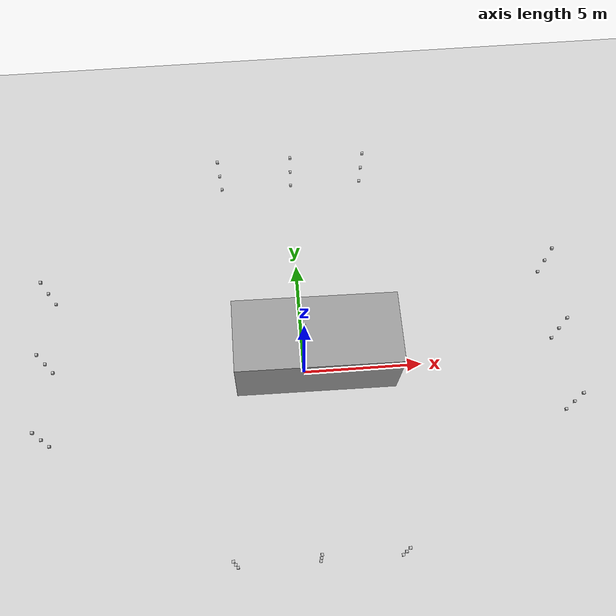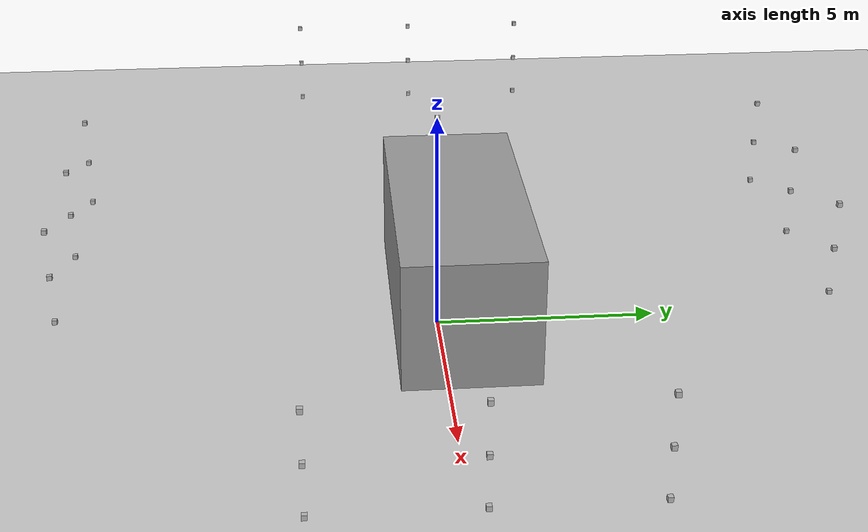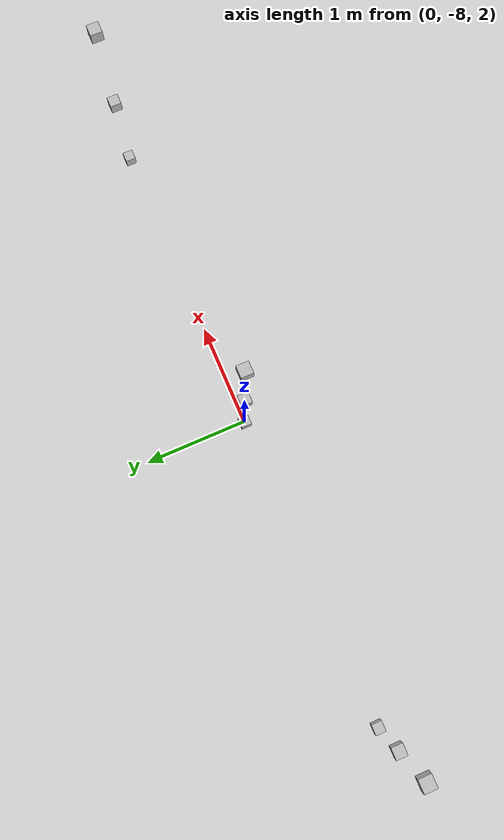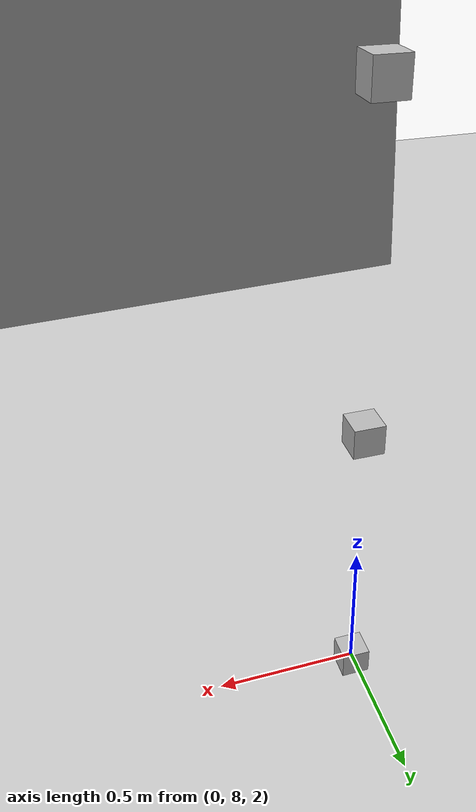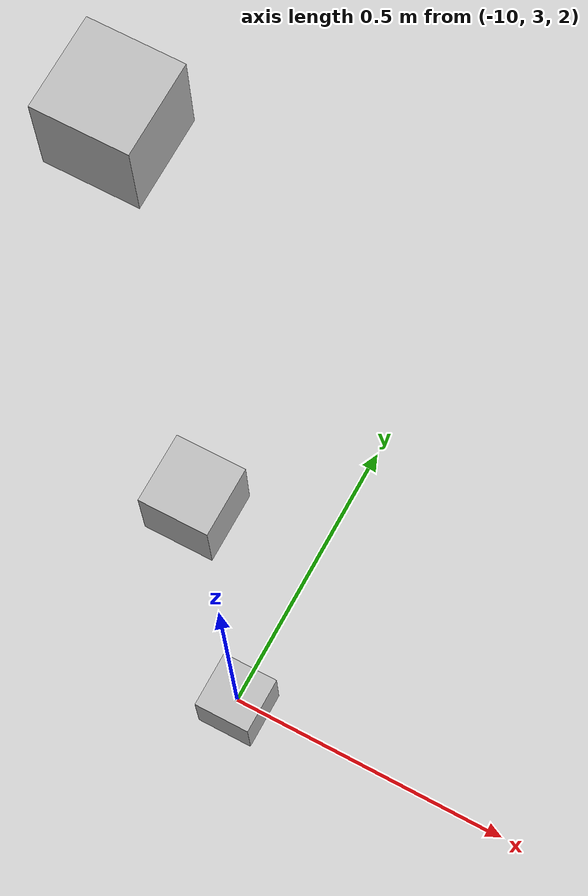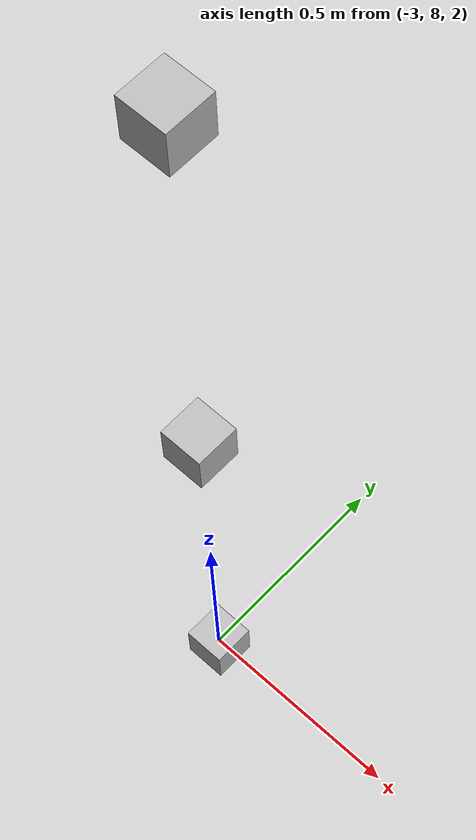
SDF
<sdf version="1.5">
 <world name="default">
  <light name="sun" type="directional">
   <pose>0 0 10 0 -0 0</pose>
   <diffuse>0.8 0.8 0.8 1</diffuse>
   <specular>0.2 0.2 0.2 1</specular>
   <attenuation>
    <range>1000</range>
    <constant>0.9</constant>
    <linear>0.01</linear>
    <quadratic>0.001</quadratic>
   </attenuation>
   <direction>-0.5 0.1 -0.9</direction>
  </light>
  <model name="ground_plane">
   <static>1</static>
   <link name="link">
    <collision name="collision">
     <geometry><plane><normal>0 0 1</normal><size>100 100</size></plane></geometry>
     <surface><friction><ode><mu>100</mu><mu2>50</mu2></ode></friction></surface>
    </collision>
    <visual name="visual">
     <cast_shadows>0</cast_shadows>
     <geometry><plane><normal>0 0 1</normal><size>100 100</size></plane></geometry>
     <material>
      <script><uri>file://media/materials/scripts/gazebo.material</uri><name>Gazebo/Grey</name></script>
     </material>
    </visual>
   </link>
  </model>
  <physics name="default_physics" default="0" type="ode">
   <max_step_size>0.001</max_step_size>
   <real_time_factor>1</real_time_factor>
   <real_time_update_rate>1000</real_time_update_rate>
   <gravity>0 0 -9.8</gravity>
   <magnetic_field>6e-06 2.3e-05 -4.2e-05</magnetic_field>
  </physics>
  <scene><ambient>0.4 0.4 0.4 1</ambient><background>0.7 0.7 0.7 1</background><shadows>0</shadows></scene>
  <spherical_coordinates>
   <surface_model>EARTH_WGS84</surface_model>
   <latitude_deg>0</latitude_deg>
   <longitude_deg>0</longitude_deg>
   <elevation>0</elevation>
   <heading_deg>0</heading_deg>
  </spherical_coordinates>
  <model name="camera_static_lg_left">
   <link name="camera::camera::link">
    <inertial>
     <mass>0.1</mass>
     <inertia>
      <ixx>0.000166667</ixx>
      <iyy>0.000166667</iyy>
      <izz>0.000166667</izz>
      <ixy>0</ixy>
      <ixz>0</ixz>
      <iyz>0</iyz>
     </inertia>
    </inertial>
    <sensor name="camera" type="camera">
     <camera name="__default__">
      <horizontal_fov>1.047</horizontal_fov>
      <image><width>800</width><height>800</height></image>
      <clip><near>0.1</near><far>100</far></clip>
     </camera>
     <always_on>1</always_on>
     <update_rate>30</update_rate>
     <visualize>1</visualize>
    </sensor>
    <visual name="visual">
     <geometry><box><size>0.1 0.1 0.1</size></box></geometry>
     <material><shader type="pixel"/></material>
    </visual>
    <collision name="collision">
     <geometry><box><size>0.1 0.1 0.1</size></box></geometry>
     <surface>
      <friction><ode><mu>1</mu><mu2>1</mu2><fdir1>0 0 0</fdir1><slip1>0</slip1><slip2>0</slip2></ode></friction>
      <bounce><restitution_coefficient>0</restitution_coefficient><threshold>1e+06</threshold></bounce>
      <contact>
       <collide_without_contact>0</collide_without_contact>
       <collide_without_contact_bitmask>1</collide_without_contact_bitmask>
       <collide_bitmask>1</collide_bitmask>
       <ode>
        <soft_cfm>0</soft_cfm>
        <soft_erp>0.2</soft_erp>
        <kp>1e+13</kp>
        <kd>1</kd>
        <max_vel>0.01</max_vel>
        <min_depth>0</min_depth>
       </ode>
       <bullet>
        <split_impulse>1</split_impulse>
        <split_impulse_penetration_threshold>-0.01</split_impulse_penetration_threshold>
        <soft_cfm>0</soft_cfm>
        <soft_erp>0.2</soft_erp>
        <kp>1e+13</kp>
        <kd>1</kd>
       </bullet>
      </contact>
     </surface>
    </collision>
   </link>
   <static>1</static>
   <pose>-10 0 2 0 -0 0</pose>
  </model>
  <model name="camera_static_lg_down">
   <link name="camera::camera::link">
    <inertial>
     <mass>0.1</mass>
     <inertia>
      <ixx>0.000166667</ixx>
      <iyy>0.000166667</iyy>
      <izz>0.000166667</izz>
      <ixy>0</ixy>
      <ixz>0</ixz>
      <iyz>0</iyz>
     </inertia>
    </inertial>
    <sensor name="camera" type="camera">
     <camera name="__default__">
      <horizontal_fov>1.047</horizontal_fov>
      <image><width>800</width><height>800</height></image>
      <clip><near>0.1</near><far>100</far></clip>
     </camera>
     <always_on>1</always_on>
     <update_rate>30</update_rate>
     <visualize>1</visualize>
    </sensor>
    <visual name="visual">
     <geometry><box><size>0.1 0.1 0.1</size></box></geometry>
     <material><shader type="pixel"/></material>
    </visual>
    <collision name="collision">
     <geometry><box><size>0.1 0.1 0.1</size></box></geometry>
     <surface>
      <friction><ode><mu>1</mu><mu2>1</mu2><fdir1>0 0 0</fdir1><slip1>0</slip1><slip2>0</slip2></ode></friction>
      <bounce><restitution_coefficient>0</restitution_coefficient><threshold>1e+06</threshold></bounce>
      <contact>
       <collide_without_contact>0</collide_without_contact>
       <collide_without_contact_bitmask>1</collide_without_contact_bitmask>
       <collide_bitmask>1</collide_bitmask>
       <ode>
        <soft_cfm>0</soft_cfm>
        <soft_erp>0.2</soft_erp>
        <kp>1e+13</kp>
        <kd>1</kd>
        <max_vel>0.01</max_vel>
        <min_depth>0</min_depth>
       </ode>
       <bullet>
        <split_impulse>1</split_impulse>
        <split_impulse_penetration_threshold>-0.01</split_impulse_penetration_threshold>
        <soft_cfm>0</soft_cfm>
        <soft_erp>0.2</soft_erp>
        <kp>1e+13</kp>
        <kd>1</kd>
       </bullet>
      </contact>
     </surface>
    </collision>
   </link>
   <static>1</static>
   <pose>0 -8 2 0 -0 1.57</pose>
  </model>
  <model name="camera_static_lg_right">
   <link name="camera::camera::link">
    <inertial>
     <mass>0.1</mass>
     <inertia>
      <ixx>0.000166667</ixx>
      <iyy>0.000166667</iyy>
      <izz>0.000166667</izz>
      <ixy>0</ixy>
      <ixz>0</ixz>
      <iyz>0</iyz>
     </inertia>
    </inertial>
    <sensor name="camera" type="camera">
     <camera name="__default__">
      <horizontal_fov>1.047</horizontal_fov>
      <image><width>800</width><height>800</height></image>
      <clip><near>0.1</near><far>100</far></clip>
     </camera>
     <always_on>1</always_on>
     <update_rate>30</update_rate>
     <visualize>1</visualize>
    </sensor>
    <visual name="visual">
     <geometry><box><size>0.1 0.1 0.1</size></box></geometry>
     <material><shader type="pixel"/></material>
    </visual>
    <collision name="collision">
     <geometry><box><size>0.1 0.1 0.1</size></box></geometry>
     <surface>
      <friction><ode><mu>1</mu><mu2>1</mu2><fdir1>0 0 0</fdir1><slip1>0</slip1><slip2>0</slip2></ode></friction>
      <bounce><restitution_coefficient>0</restitution_coefficient><threshold>1e+06</threshold></bounce>
      <contact>
       <collide_without_contact>0</collide_without_contact>
       <collide_without_contact_bitmask>1</collide_without_contact_bitmask>
       <collide_bitmask>1</collide_bitmask>
       <ode>
        <soft_cfm>0</soft_cfm>
        <soft_erp>0.2</soft_erp>
        <kp>1e+13</kp>
        <kd>1</kd>
        <max_vel>0.01</max_vel>
        <min_depth>0</min_depth>
       </ode>
       <bullet>
        <split_impulse>1</split_impulse>
        <split_impulse_penetration_threshold>-0.01</split_impulse_penetration_threshold>
        <soft_cfm>0</soft_cfm>
        <soft_erp>0.2</soft_erp>
        <kp>1e+13</kp>
        <kd>1</kd>
       </bullet>
      </contact>
     </surface>
    </collision>
   </link>
   <static>1</static>
   <pose>10 0 2 0 -0 3.14</pose>
  </model>
  <model name="camera_static_lg_up">
   <link name="camera::camera::link">
    <inertial>
     <mass>0.1</mass>
     <inertia>
      <ixx>0.000166667</ixx>
      <iyy>0.000166667</iyy>
      <izz>0.000166667</izz>
      <ixy>0</ixy>
      <ixz>0</ixz>
      <iyz>0</iyz>
     </inertia>
    </inertial>
    <sensor name="camera" type="camera">
     <camera name="__default__">
      <horizontal_fov>1.047</horizontal_fov>
      <image><width>800</width><height>800</height></image>
      <clip><near>0.1</near><far>100</far></clip>
     </camera>
     <always_on>1</always_on>
     <update_rate>30</update_rate>
     <visualize>1</visualize>
    </sensor>
    <visual name="visual">
     <geometry><box><size>0.1 0.1 0.1</size></box></geometry>
     <material><shader type="pixel"/></material>
    </visual>
    <collision name="collision">
     <geometry><box><size>0.1 0.1 0.1</size></box></geometry>
     <surface>
      <friction><ode><mu>1</mu><mu2>1</mu2><fdir1>0 0 0</fdir1><slip1>0</slip1><slip2>0</slip2></ode></friction>
      <bounce><restitution_coefficient>0</restitution_coefficient><threshold>1e+06</threshold></bounce>
      <contact>
       <collide_without_contact>0</collide_without_contact>
       <collide_without_contact_bitmask>1</collide_without_contact_bitmask>
       <collide_bitmask>1</collide_bitmask>
       <ode>
        <soft_cfm>0</soft_cfm>
        <soft_erp>0.2</soft_erp>
        <kp>1e+13</kp>
        <kd>1</kd>
        <max_vel>0.01</max_vel>
        <min_depth>0</min_depth>
       </ode>
       <bullet>
        <split_impulse>1</split_impulse>
        <split_impulse_penetration_threshold>-0.01</split_impulse_penetration_threshold>
        <soft_cfm>0</soft_cfm>
        <soft_erp>0.2</soft_erp>
        <kp>1e+13</kp>
        <kd>1</kd>
       </bullet>
      </contact>
     </surface>
    </collision>
   </link>
   <static>1</static>
   <pose>0 8 2 0 0 -1.57</pose>
  </model>
  <model name="camera_static_lg_left_1">
   <link name="camera::camera::link">
    <inertial>
     <mass>0.1</mass>
     <inertia>
      <ixx>0.000166667</ixx>
      <iyy>0.000166667</iyy>
      <izz>0.000166667</izz>
      <ixy>0</ixy>
      <ixz>0</ixz>
      <iyz>0</iyz>
     </inertia>
    </inertial>
    <sensor name="camera" type="camera">
     <camera name="__default__">
      <horizontal_fov>1.047</horizontal_fov>
      <image><width>800</width><height>800</height></image>
      <clip><near>0.1</near><far>100</far></clip>
     </camera>
     <always_on>1</always_on>
     <update_rate>30</update_rate>
     <visualize>1</visualize>
    </sensor>
    <visual name="visual">
     <geometry><box><size>0.1 0.1 0.1</size></box></geometry>
     <material><shader type="pixel"/></material>
    </visual>
    <collision name="collision">
     <geometry><box><size>0.1 0.1 0.1</size></box></geometry>
     <surface>
      <friction><ode><mu>1</mu><mu2>1</mu2><fdir1>0 0 0</fdir1><slip1>0</slip1><slip2>0</slip2></ode></friction>
      <bounce><restitution_coefficient>0</restitution_coefficient><threshold>1e+06</threshold></bounce>
      <contact>
       <collide_without_contact>0</collide_without_contact>
       <collide_without_contact_bitmask>1</collide_without_contact_bitmask>
       <collide_bitmask>1</collide_bitmask>
       <ode>
        <soft_cfm>0</soft_cfm>
        <soft_erp>0.2</soft_erp>
        <kp>1e+13</kp>
        <kd>1</kd>
        <max_vel>0.01</max_vel>
        <min_depth>0</min_depth>
       </ode>
       <bullet>
        <split_impulse>1</split_impulse>
        <split_impulse_penetration_threshold>-0.01</split_impulse_penetration_threshold>
        <soft_cfm>0</soft_cfm>
        <soft_erp>0.2</soft_erp>
        <kp>1e+13</kp>
        <kd>1</kd>
       </bullet>
      </contact>
     </surface>
    </collision>
   </link>
   <static>1</static>
   <pose>-10 3 2 0 -0 0</pose>
  </model>
  <model name="camera_static_lg_down_1">
   <link name="camera::camera::link">
    <inertial>
     <mass>0.1</mass>
     <inertia>
      <ixx>0.000166667</ixx>
      <iyy>0.000166667</iyy>
      <izz>0.000166667</izz>
      <ixy>0</ixy>
      <ixz>0</ixz>
      <iyz>0</iyz>
     </inertia>
    </inertial>
    <sensor name="camera" type="camera">
     <camera name="__default__">
      <horizontal_fov>1.047</horizontal_fov>
      <image><width>800</width><height>800</height></image>
      <clip><near>0.1</near><far>100</far></clip>
     </camera>
     <always_on>1</always_on>
     <update_rate>30</update_rate>
     <visualize>1</visualize>
    </sensor>
    <visual name="visual">
     <geometry><box><size>0.1 0.1 0.1</size></box></geometry>
     <material><shader type="pixel"/></material>
    </visual>
    <collision name="collision">
     <geometry><box><size>0.1 0.1 0.1</size></box></geometry>
     <surface>
      <friction><ode><mu>1</mu><mu2>1</mu2><fdir1>0 0 0</fdir1><slip1>0</slip1><slip2>0</slip2></ode></friction>
      <bounce><restitution_coefficient>0</restitution_coefficient><threshold>1e+06</threshold></bounce>
      <contact>
       <collide_without_contact>0</collide_without_contact>
       <collide_without_contact_bitmask>1</collide_without_contact_bitmask>
       <collide_bitmask>1</collide_bitmask>
       <ode>
        <soft_cfm>0</soft_cfm>
        <soft_erp>0.2</soft_erp>
        <kp>1e+13</kp>
        <kd>1</kd>
        <max_vel>0.01</max_vel>
        <min_depth>0</min_depth>
       </ode>
       <bullet>
        <split_impulse>1</split_impulse>
        <split_impulse_penetration_threshold>-0.01</split_impulse_penetration_threshold>
        <soft_cfm>0</soft_cfm>
        <soft_erp>0.2</soft_erp>
        <kp>1e+13</kp>
        <kd>1</kd>
       </bullet>
      </contact>
     </surface>
    </collision>
   </link>
   <static>1</static>
   <pose>-3 -8 2 0 -0 1.57</pose>
  </model>
  <model name="camera_static_lg_right_1">
   <link name="camera::camera::link">
    <inertial>
     <mass>0.1</mass>
     <inertia>
      <ixx>0.000166667</ixx>
      <iyy>0.000166667</iyy>
      <izz>0.000166667</izz>
      <ixy>0</ixy>
      <ixz>0</ixz>
      <iyz>0</iyz>
     </inertia>
    </inertial>
    <sensor name="camera" type="camera">
     <camera name="__default__">
      <horizontal_fov>1.047</horizontal_fov>
      <image><width>800</width><height>800</height></image>
      <clip><near>0.1</near><far>100</far></clip>
     </camera>
     <always_on>1</always_on>
     <update_rate>30</update_rate>
     <visualize>1</visualize>
    </sensor>
    <visual name="visual">
     <geometry><box><size>0.1 0.1 0.1</size></box></geometry>
     <material><shader type="pixel"/></material>
    </visual>
    <collision name="collision">
     <geometry><box><size>0.1 0.1 0.1</size></box></geometry>
     <surface>
      <friction><ode><mu>1</mu><mu2>1</mu2><fdir1>0 0 0</fdir1><slip1>0</slip1><slip2>0</slip2></ode></friction>
      <bounce><restitution_coefficient>0</restitution_coefficient><threshold>1e+06</threshold></bounce>
      <contact>
       <collide_without_contact>0</collide_without_contact>
       <collide_without_contact_bitmask>1</collide_without_contact_bitmask>
       <collide_bitmask>1</collide_bitmask>
       <ode>
        <soft_cfm>0</soft_cfm>
        <soft_erp>0.2</soft_erp>
        <kp>1e+13</kp>
        <kd>1</kd>
        <max_vel>0.01</max_vel>
        <min_depth>0</min_depth>
       </ode>
       <bullet>
        <split_impulse>1</split_impulse>
        <split_impulse_penetration_threshold>-0.01</split_impulse_penetration_threshold>
        <soft_cfm>0</soft_cfm>
        <soft_erp>0.2</soft_erp>
        <kp>1e+13</kp>
        <kd>1</kd>
       </bullet>
      </contact>
     </surface>
    </collision>
   </link>
   <static>1</static>
   <pose>10 -3 2 0 -0 3.14</pose>
  </model>
  <model name="camera_static_lg_up_1">
   <link name="camera::camera::link">
    <inertial>
     <mass>0.1</mass>
     <inertia>
      <ixx>0.000166667</ixx>
      <iyy>0.000166667</iyy>
      <izz>0.000166667</izz>
      <ixy>0</ixy>
      <ixz>0</ixz>
      <iyz>0</iyz>
     </inertia>
    </inertial>
    <sensor name="camera" type="camera">
     <camera name="__default__">
      <horizontal_fov>1.047</horizontal_fov>
      <image><width>800</width><height>800</height></image>
      <clip><near>0.1</near><far>100</far></clip>
     </camera>
     <always_on>1</always_on>
     <update_rate>30</update_rate>
     <visualize>1</visualize>
    </sensor>
    <visual name="visual">
     <geometry><box><size>0.1 0.1 0.1</size></box></geometry>
     <material><shader type="pixel"/></material>
    </visual>
    <collision name="collision">
     <geometry><box><size>0.1 0.1 0.1</size></box></geometry>
     <surface>
      <friction><ode><mu>1</mu><mu2>1</mu2><fdir1>0 0 0</fdir1><slip1>0</slip1><slip2>0</slip2></ode></friction>
      <bounce><restitution_coefficient>0</restitution_coefficient><threshold>1e+06</threshold></bounce>
      <contact>
       <collide_without_contact>0</collide_without_contact>
       <collide_without_contact_bitmask>1</collide_without_contact_bitmask>
       <collide_bitmask>1</collide_bitmask>
       <ode>
        <soft_cfm>0</soft_cfm>
        <soft_erp>0.2</soft_erp>
        <kp>1e+13</kp>
        <kd>1</kd>
        <max_vel>0.01</max_vel>
        <min_depth>0</min_depth>
       </ode>
       <bullet>
        <split_impulse>1</split_impulse>
        <split_impulse_penetration_threshold>-0.01</split_impulse_penetration_threshold>
        <soft_cfm>0</soft_cfm>
        <soft_erp>0.2</soft_erp>
        <kp>1e+13</kp>
        <kd>1</kd>
       </bullet>
      </contact>
     </surface>
    </collision>
   </link>
   <static>1</static>
   <pose>3 8 2 0 0 -1.57</pose>
  </model>
  <model name="camera_static_lg_left_2">
   <link name="camera::camera::link">
    <inertial>
     <mass>0.1</mass>
     <inertia>
      <ixx>0.000166667</ixx>
      <iyy>0.000166667</iyy>
      <izz>0.000166667</izz>
      <ixy>0</ixy>
      <ixz>0</ixz>
      <iyz>0</iyz>
     </inertia>
    </inertial>
    <sensor name="camera" type="camera">
     <camera name="__default__">
      <horizontal_fov>1.047</horizontal_fov>
      <image><width>800</width><height>800</height></image>
      <clip><near>0.1</near><far>100</far></clip>
     </camera>
     <always_on>1</always_on>
     <update_rate>30</update_rate>
     <visualize>1</visualize>
    </sensor>
    <visual name="visual">
     <geometry><box><size>0.1 0.1 0.1</size></box></geometry>
     <material><shader type="pixel"/></material>
    </visual>
    <collision name="collision">
     <geometry><box><size>0.1 0.1 0.1</size></box></geometry>
     <surface>
      <friction><ode><mu>1</mu><mu2>1</mu2><fdir1>0 0 0</fdir1><slip1>0</slip1><slip2>0</slip2></ode></friction>
      <bounce><restitution_coefficient>0</restitution_coefficient><threshold>1e+06</threshold></bounce>
      <contact>
       <collide_without_contact>0</collide_without_contact>
       <collide_without_contact_bitmask>1</collide_without_contact_bitmask>
       <collide_bitmask>1</collide_bitmask>
       <ode>
        <soft_cfm>0</soft_cfm>
        <soft_erp>0.2</soft_erp>
        <kp>1e+13</kp>
        <kd>1</kd>
        <max_vel>0.01</max_vel>
        <min_depth>0</min_depth>
       </ode>
       <bullet>
        <split_impulse>1</split_impulse>
        <split_impulse_penetration_threshold>-0.01</split_impulse_penetration_threshold>
        <soft_cfm>0</soft_cfm>
        <soft_erp>0.2</soft_erp>
        <kp>1e+13</kp>
        <kd>1</kd>
       </bullet>
      </contact>
     </surface>
    </collision>
   </link>
   <static>1</static>
   <pose>-10 -3 2 0 -0 0</pose>
  </model>
  <model name="camera_static_lg_down_2">
   <link name="camera::camera::link">
    <inertial>
     <mass>0.1</mass>
     <inertia>
      <ixx>0.000166667</ixx>
      <iyy>0.000166667</iyy>
      <izz>0.000166667</izz>
      <ixy>0</ixy>
      <ixz>0</ixz>
      <iyz>0</iyz>
     </inertia>
    </inertial>
    <sensor name="camera" type="camera">
     <camera name="__default__">
      <horizontal_fov>1.047</horizontal_fov>
      <image><width>800</width><height>800</height></image>
      <clip><near>0.1</near><far>100</far></clip>
     </camera>
     <always_on>1</always_on>
     <update_rate>30</update_rate>
     <visualize>1</visualize>
    </sensor>
    <visual name="visual">
     <geometry><box><size>0.1 0.1 0.1</size></box></geometry>
     <material><shader type="pixel"/></material>
    </visual>
    <collision name="collision">
     <geometry><box><size>0.1 0.1 0.1</size></box></geometry>
     <surface>
      <friction><ode><mu>1</mu><mu2>1</mu2><fdir1>0 0 0</fdir1><slip1>0</slip1><slip2>0</slip2></ode></friction>
      <bounce><restitution_coefficient>0</restitution_coefficient><threshold>1e+06</threshold></bounce>
      <contact>
       <collide_without_contact>0</collide_without_contact>
       <collide_without_contact_bitmask>1</collide_without_contact_bitmask>
       <collide_bitmask>1</collide_bitmask>
       <ode>
        <soft_cfm>0</soft_cfm>
        <soft_erp>0.2</soft_erp>
        <kp>1e+13</kp>
        <kd>1</kd>
        <max_vel>0.01</max_vel>
        <min_depth>0</min_depth>
       </ode>
       <bullet>
        <split_impulse>1</split_impulse>
        <split_impulse_penetration_threshold>-0.01</split_impulse_penetration_threshold>
        <soft_cfm>0</soft_cfm>
        <soft_erp>0.2</soft_erp>
        <kp>1e+13</kp>
        <kd>1</kd>
       </bullet>
      </contact>
     </surface>
    </collision>
   </link>
   <static>1</static>
   <pose>3 -8 2 0 -0 1.57</pose>
  </model>
  <model name="camera_static_lg_right_2">
   <link name="camera::camera::link">
    <inertial>
     <mass>0.1</mass>
     <inertia>
      <ixx>0.000166667</ixx>
      <iyy>0.000166667</iyy>
      <izz>0.000166667</izz>
      <ixy>0</ixy>
      <ixz>0</ixz>
      <iyz>0</iyz>
     </inertia>
    </inertial>
    <sensor name="camera" type="camera">
     <camera name="__default__">
      <horizontal_fov>1.047</horizontal_fov>
      <image><width>800</width><height>800</height></image>
      <clip><near>0.1</near><far>100</far></clip>
     </camera>
     <always_on>1</always_on>
     <update_rate>30</update_rate>
     <visualize>1</visualize>
    </sensor>
    <visual name="visual">
     <geometry><box><size>0.1 0.1 0.1</size></box></geometry>
     <material><shader type="pixel"/></material>
    </visual>
    <collision name="collision">
     <geometry><box><size>0.1 0.1 0.1</size></box></geometry>
     <surface>
      <friction><ode><mu>1</mu><mu2>1</mu2><fdir1>0 0 0</fdir1><slip1>0</slip1><slip2>0</slip2></ode></friction>
      <bounce><restitution_coefficient>0</restitution_coefficient><threshold>1e+06</threshold></bounce>
      <contact>
       <collide_without_contact>0</collide_without_contact>
       <collide_without_contact_bitmask>1</collide_without_contact_bitmask>
       <collide_bitmask>1</collide_bitmask>
       <ode>
        <soft_cfm>0</soft_cfm>
        <soft_erp>0.2</soft_erp>
        <kp>1e+13</kp>
        <kd>1</kd>
        <max_vel>0.01</max_vel>
        <min_depth>0</min_depth>
       </ode>
       <bullet>
        <split_impulse>1</split_impulse>
        <split_impulse_penetration_threshold>-0.01</split_impulse_penetration_threshold>
        <soft_cfm>0</soft_cfm>
        <soft_erp>0.2</soft_erp>
        <kp>1e+13</kp>
        <kd>1</kd>
       </bullet>
      </contact>
     </surface>
    </collision>
   </link>
   <static>1</static>
   <pose>10 3 2 0 -0 3.14</pose>
  </model>
  <model name="camera_static_lg_up_2">
   <link name="camera::camera::link">
    <inertial>
     <mass>0.1</mass>
     <inertia>
      <ixx>0.000166667</ixx>
      <iyy>0.000166667</iyy>
      <izz>0.000166667</izz>
      <ixy>0</ixy>
      <ixz>0</ixz>
      <iyz>0</iyz>
     </inertia>
    </inertial>
    <sensor name="camera" type="camera">
     <camera name="__default__">
      <horizontal_fov>1.047</horizontal_fov>
      <image><width>800</width><height>800</height></image>
      <clip><near>0.1</near><far>100</far></clip>
     </camera>
     <always_on>1</always_on>
     <update_rate>30</update_rate>
     <visualize>1</visualize>
    </sensor>
    <visual name="visual">
     <geometry><box><size>0.1 0.1 0.1</size></box></geometry>
     <material><shader type="pixel"/></material>
    </visual>
    <collision name="collision">
     <geometry><box><size>0.1 0.1 0.1</size></box></geometry>
     <surface>
      <friction><ode><mu>1</mu><mu2>1</mu2><fdir1>0 0 0</fdir1><slip1>0</slip1><slip2>0</slip2></ode></friction>
      <bounce><restitution_coefficient>0</restitution_coefficient><threshold>1e+06</threshold></bounce>
      <contact>
       <collide_without_contact>0</collide_without_contact>
       <collide_without_contact_bitmask>1</collide_without_contact_bitmask>
       <collide_bitmask>1</collide_bitmask>
       <ode>
        <soft_cfm>0</soft_cfm>
        <soft_erp>0.2</soft_erp>
        <kp>1e+13</kp>
        <kd>1</kd>
        <max_vel>0.01</max_vel>
        <min_depth>0</min_depth>
       </ode>
       <bullet>
        <split_impulse>1</split_impulse>
        <split_impulse_penetration_threshold>-0.01</split_impulse_penetration_threshold>
        <soft_cfm>0</soft_cfm>
        <soft_erp>0.2</soft_erp>
        <kp>1e+13</kp>
        <kd>1</kd>
       </bullet>
      </contact>
     </surface>
    </collision>
   </link>
   <static>1</static>
   <pose>-3 8 2 0 0 -1.57</pose>
  </model>
  <model name="camera_static_l0_left">
   <link name="camera::camera::link">
    <inertial>
     <mass>0.1</mass>
     <inertia>
      <ixx>0.000166667</ixx>
      <iyy>0.000166667</iyy>
      <izz>0.000166667</izz>
      <ixy>0</ixy>
      <ixz>0</ixz>
      <iyz>0</iyz>
     </inertia>
    </inertial>
    <sensor name="camera" type="camera">
     <camera name="__default__">
      <horizontal_fov>1.047</horizontal_fov>
      <image><width>800</width><height>800</height></image>
      <clip><near>0.1</near><far>100</far></clip>
     </camera>
     <always_on>1</always_on>
     <update_rate>30</update_rate>
     <visualize>1</visualize>
    </sensor>
    <visual name="visual">
     <geometry><box><size>0.1 0.1 0.1</size></box></geometry>
     <material><shader type="pixel"/></material>
    </visual>
    <collision name="collision">
     <geometry><box><size>0.1 0.1 0.1</size></box></geometry>
     <surface>
      <friction><ode><mu>1</mu><mu2>1</mu2><fdir1>0 0 0</fdir1><slip1>0</slip1><slip2>0</slip2></ode></friction>
      <bounce><restitution_coefficient>0</restitution_coefficient><threshold>1e+06</threshold></bounce>
      <contact>
       <collide_without_contact>0</collide_without_contact>
       <collide_without_contact_bitmask>1</collide_without_contact_bitmask>
       <collide_bitmask>1</collide_bitmask>
       <ode>
        <soft_cfm>0</soft_cfm>
        <soft_erp>0.2</soft_erp>
        <kp>1e+13</kp>
        <kd>1</kd>
        <max_vel>0.01</max_vel>
        <min_depth>0</min_depth>
       </ode>
       <bullet>
        <split_impulse>1</split_impulse>
        <split_impulse_penetration_threshold>-0.01</split_impulse_penetration_threshold>
        <soft_cfm>0</soft_cfm>
        <soft_erp>0.2</soft_erp>
        <kp>1e+13</kp>
        <kd>1</kd>
       </bullet>
      </contact>
     </surface>
    </collision>
   </link>
   <static>1</static>
   <pose>-10 0 3 0 -0 0</pose>
  </model>
  <model name="camera_static_l0_down">
   <link name="camera::camera::link">
    <inertial>
     <mass>0.1</mass>
     <inertia>
      <ixx>0.000166667</ixx>
      <iyy>0.000166667</iyy>
      <izz>0.000166667</izz>
      <ixy>0</ixy>
      <ixz>0</ixz>
      <iyz>0</iyz>
     </inertia>
    </inertial>
    <sensor name="camera" type="camera">
     <camera name="__default__">
      <horizontal_fov>1.047</horizontal_fov>
      <image><width>800</width><height>800</height></image>
      <clip><near>0.1</near><far>100</far></clip>
     </camera>
     <always_on>1</always_on>
     <update_rate>30</update_rate>
     <visualize>1</visualize>
    </sensor>
    <visual name="visual">
     <geometry><box><size>0.1 0.1 0.1</size></box></geometry>
     <material><shader type="pixel"/></material>
    </visual>
    <collision name="collision">
     <geometry><box><size>0.1 0.1 0.1</size></box></geometry>
     <surface>
      <friction><ode><mu>1</mu><mu2>1</mu2><fdir1>0 0 0</fdir1><slip1>0</slip1><slip2>0</slip2></ode></friction>
      <bounce><restitution_coefficient>0</restitution_coefficient><threshold>1e+06</threshold></bounce>
      <contact>
       <collide_without_contact>0</collide_without_contact>
       <collide_without_contact_bitmask>1</collide_without_contact_bitmask>
       <collide_bitmask>1</collide_bitmask>
       <ode>
        <soft_cfm>0</soft_cfm>
        <soft_erp>0.2</soft_erp>
        <kp>1e+13</kp>
        <kd>1</kd>
        <max_vel>0.01</max_vel>
        <min_depth>0</min_depth>
       </ode>
       <bullet>
        <split_impulse>1</split_impulse>
        <split_impulse_penetration_threshold>-0.01</split_impulse_penetration_threshold>
        <soft_cfm>0</soft_cfm>
        <soft_erp>0.2</soft_erp>
        <kp>1e+13</kp>
        <kd>1</kd>
       </bullet>
      </contact>
     </surface>
    </collision>
   </link>
   <static>1</static>
   <pose>0 -8 3 0 -0 1.57</pose>
  </model>
  <model name="camera_static_l0_right">
   <link name="camera::camera::link">
    <inertial>
     <mass>0.1</mass>
     <inertia>
      <ixx>0.000166667</ixx>
      <iyy>0.000166667</iyy>
      <izz>0.000166667</izz>
      <ixy>0</ixy>
      <ixz>0</ixz>
      <iyz>0</iyz>
     </inertia>
    </inertial>
    <sensor name="camera" type="camera">
     <camera name="__default__">
      <horizontal_fov>1.047</horizontal_fov>
      <image><width>800</width><height>800</height></image>
      <clip><near>0.1</near><far>100</far></clip>
     </camera>
     <always_on>1</always_on>
     <update_rate>30</update_rate>
     <visualize>1</visualize>
    </sensor>
    <visual name="visual">
     <geometry><box><size>0.1 0.1 0.1</size></box></geometry>
     <material><shader type="pixel"/></material>
    </visual>
    <collision name="collision">
     <geometry><box><size>0.1 0.1 0.1</size></box></geometry>
     <surface>
      <friction><ode><mu>1</mu><mu2>1</mu2><fdir1>0 0 0</fdir1><slip1>0</slip1><slip2>0</slip2></ode></friction>
      <bounce><restitution_coefficient>0</restitution_coefficient><threshold>1e+06</threshold></bounce>
      <contact>
       <collide_without_contact>0</collide_without_contact>
       <collide_without_contact_bitmask>1</collide_without_contact_bitmask>
       <collide_bitmask>1</collide_bitmask>
       <ode>
        <soft_cfm>0</soft_cfm>
        <soft_erp>0.2</soft_erp>
        <kp>1e+13</kp>
        <kd>1</kd>
        <max_vel>0.01</max_vel>
        <min_depth>0</min_depth>
       </ode>
       <bullet>
        <split_impulse>1</split_impulse>
        <split_impulse_penetration_threshold>-0.01</split_impulse_penetration_threshold>
        <soft_cfm>0</soft_cfm>
        <soft_erp>0.2</soft_erp>
        <kp>1e+13</kp>
        <kd>1</kd>
       </bullet>
      </contact>
     </surface>
    </collision>
   </link>
   <static>1</static>
   <pose>10 0 3 0 -0 3.14</pose>
  </model>
  <model name="camera_static_l0_up">
   <link name="camera::camera::link">
    <inertial>
     <mass>0.1</mass>
     <inertia>
      <ixx>0.000166667</ixx>
      <iyy>0.000166667</iyy>
      <izz>0.000166667</izz>
      <ixy>0</ixy>
      <ixz>0</ixz>
      <iyz>0</iyz>
     </inertia>
    </inertial>
    <sensor name="camera" type="camera">
     <camera name="__default__">
      <horizontal_fov>1.047</horizontal_fov>
      <image><width>800</width><height>800</height></image>
      <clip><near>0.1</near><far>100</far></clip>
     </camera>
     <always_on>1</always_on>
     <update_rate>30</update_rate>
     <visualize>1</visualize>
    </sensor>
    <visual name="visual">
     <geometry><box><size>0.1 0.1 0.1</size></box></geometry>
     <material><shader type="pixel"/></material>
    </visual>
    <collision name="collision">
     <geometry><box><size>0.1 0.1 0.1</size></box></geometry>
     <surface>
      <friction><ode><mu>1</mu><mu2>1</mu2><fdir1>0 0 0</fdir1><slip1>0</slip1><slip2>0</slip2></ode></friction>
      <bounce><restitution_coefficient>0</restitution_coefficient><threshold>1e+06</threshold></bounce>
      <contact>
       <collide_without_contact>0</collide_without_contact>
       <collide_without_contact_bitmask>1</collide_without_contact_bitmask>
       <collide_bitmask>1</collide_bitmask>
       <ode>
        <soft_cfm>0</soft_cfm>
        <soft_erp>0.2</soft_erp>
        <kp>1e+13</kp>
        <kd>1</kd>
        <max_vel>0.01</max_vel>
        <min_depth>0</min_depth>
       </ode>
       <bullet>
        <split_impulse>1</split_impulse>
        <split_impulse_penetration_threshold>-0.01</split_impulse_penetration_threshold>
        <soft_cfm>0</soft_cfm>
        <soft_erp>0.2</soft_erp>
        <kp>1e+13</kp>
        <kd>1</kd>
       </bullet>
      </contact>
     </surface>
    </collision>
   </link>
   <static>1</static>
   <pose>0 8 3 0 0 -1.57</pose>
  </model>
  <model name="camera_static_l0_left_1">
   <link name="camera::camera::link">
    <inertial>
     <mass>0.1</mass>
     <inertia>
      <ixx>0.000166667</ixx>
      <iyy>0.000166667</iyy>
      <izz>0.000166667</izz>
      <ixy>0</ixy>
      <ixz>0</ixz>
      <iyz>0</iyz>
     </inertia>
    </inertial>
    <sensor name="camera" type="camera">
     <camera name="__default__">
      <horizontal_fov>1.047</horizontal_fov>
      <image><width>800</width><height>800</height></image>
      <clip><near>0.1</near><far>100</far></clip>
     </camera>
     <always_on>1</always_on>
     <update_rate>30</update_rate>
     <visualize>1</visualize>
    </sensor>
    <visual name="visual">
     <geometry><box><size>0.1 0.1 0.1</size></box></geometry>
     <material><shader type="pixel"/></material>
    </visual>
    <collision name="collision">
     <geometry><box><size>0.1 0.1 0.1</size></box></geometry>
     <surface>
      <friction><ode><mu>1</mu><mu2>1</mu2><fdir1>0 0 0</fdir1><slip1>0</slip1><slip2>0</slip2></ode></friction>
      <bounce><restitution_coefficient>0</restitution_coefficient><threshold>1e+06</threshold></bounce>
      <contact>
       <collide_without_contact>0</collide_without_contact>
       <collide_without_contact_bitmask>1</collide_without_contact_bitmask>
       <collide_bitmask>1</collide_bitmask>
       <ode>
        <soft_cfm>0</soft_cfm>
        <soft_erp>0.2</soft_erp>
        <kp>1e+13</kp>
        <kd>1</kd>
        <max_vel>0.01</max_vel>
        <min_depth>0</min_depth>
       </ode>
       <bullet>
        <split_impulse>1</split_impulse>
        <split_impulse_penetration_threshold>-0.01</split_impulse_penetration_threshold>
        <soft_cfm>0</soft_cfm>
        <soft_erp>0.2</soft_erp>
        <kp>1e+13</kp>
        <kd>1</kd>
       </bullet>
      </contact>
     </surface>
    </collision>
   </link>
   <static>1</static>
   <pose>-10 3 3 0 -0 0</pose>
  </model>
  <model name="camera_static_l0_down_1">
   <link name="camera::camera::link">
    <inertial>
     <mass>0.1</mass>
     <inertia>
      <ixx>0.000166667</ixx>
      <iyy>0.000166667</iyy>
      <izz>0.000166667</izz>
      <ixy>0</ixy>
      <ixz>0</ixz>
      <iyz>0</iyz>
     </inertia>
    </inertial>
    <sensor name="camera" type="camera">
     <camera name="__default__">
      <horizontal_fov>1.047</horizontal_fov>
      <image><width>800</width><height>800</height></image>
      <clip><near>0.1</near><far>100</far></clip>
     </camera>
     <always_on>1</always_on>
     <update_rate>30</update_rate>
     <visualize>1</visualize>
    </sensor>
    <visual name="visual">
     <geometry><box><size>0.1 0.1 0.1</size></box></geometry>
     <material><shader type="pixel"/></material>
    </visual>
    <collision name="collision">
     <geometry><box><size>0.1 0.1 0.1</size></box></geometry>
     <surface>
      <friction><ode><mu>1</mu><mu2>1</mu2><fdir1>0 0 0</fdir1><slip1>0</slip1><slip2>0</slip2></ode></friction>
      <bounce><restitution_coefficient>0</restitution_coefficient><threshold>1e+06</threshold></bounce>
      <contact>
       <collide_without_contact>0</collide_without_contact>
       <collide_without_contact_bitmask>1</collide_without_contact_bitmask>
       <collide_bitmask>1</collide_bitmask>
       <ode>
        <soft_cfm>0</soft_cfm>
        <soft_erp>0.2</soft_erp>
        <kp>1e+13</kp>
        <kd>1</kd>
        <max_vel>0.01</max_vel>
        <min_depth>0</min_depth>
       </ode>
       <bullet>
        <split_impulse>1</split_impulse>
        <split_impulse_penetration_threshold>-0.01</split_impulse_penetration_threshold>
        <soft_cfm>0</soft_cfm>
        <soft_erp>0.2</soft_erp>
        <kp>1e+13</kp>
        <kd>1</kd>
       </bullet>
      </contact>
     </surface>
    </collision>
   </link>
   <static>1</static>
   <pose>-3 -8 3 0 -0 1.57</pose>
  </model>
  <model name="camera_static_l0_right_1">
   <link name="camera::camera::link">
    <inertial>
     <mass>0.1</mass>
     <inertia>
      <ixx>0.000166667</ixx>
      <iyy>0.000166667</iyy>
      <izz>0.000166667</izz>
      <ixy>0</ixy>
      <ixz>0</ixz>
      <iyz>0</iyz>
     </inertia>
    </inertial>
    <sensor name="camera" type="camera">
     <camera name="__default__">
      <horizontal_fov>1.047</horizontal_fov>
      <image><width>800</width><height>800</height></image>
      <clip><near>0.1</near><far>100</far></clip>
     </camera>
     <always_on>1</always_on>
     <update_rate>30</update_rate>
     <visualize>1</visualize>
    </sensor>
    <visual name="visual">
     <geometry><box><size>0.1 0.1 0.1</size></box></geometry>
     <material><shader type="pixel"/></material>
    </visual>
    <collision name="collision">
     <geometry><box><size>0.1 0.1 0.1</size></box></geometry>
     <surface>
      <friction><ode><mu>1</mu><mu2>1</mu2><fdir1>0 0 0</fdir1><slip1>0</slip1><slip2>0</slip2></ode></friction>
      <bounce><restitution_coefficient>0</restitution_coefficient><threshold>1e+06</threshold></bounce>
      <contact>
       <collide_without_contact>0</collide_without_contact>
       <collide_without_contact_bitmask>1</collide_without_contact_bitmask>
       <collide_bitmask>1</collide_bitmask>
       <ode>
        <soft_cfm>0</soft_cfm>
        <soft_erp>0.2</soft_erp>
        <kp>1e+13</kp>
        <kd>1</kd>
        <max_vel>0.01</max_vel>
        <min_depth>0</min_depth>
       </ode>
       <bullet>
        <split_impulse>1</split_impulse>
        <split_impulse_penetration_threshold>-0.01</split_impulse_penetration_threshold>
        <soft_cfm>0</soft_cfm>
        <soft_erp>0.2</soft_erp>
        <kp>1e+13</kp>
        <kd>1</kd>
       </bullet>
      </contact>
     </surface>
    </collision>
   </link>
   <static>1</static>
   <pose>10 -3 3 0 -0 3.14</pose>
  </model>
  <model name="camera_static_l0_up_1">
   <link name="camera::camera::link">
    <inertial>
     <mass>0.1</mass>
     <inertia>
      <ixx>0.000166667</ixx>
      <iyy>0.000166667</iyy>
      <izz>0.000166667</izz>
      <ixy>0</ixy>
      <ixz>0</ixz>
      <iyz>0</iyz>
     </inertia>
    </inertial>
    <sensor name="camera" type="camera">
     <camera name="__default__">
      <horizontal_fov>1.047</horizontal_fov>
      <image><width>800</width><height>800</height></image>
      <clip><near>0.1</near><far>100</far></clip>
     </camera>
     <always_on>1</always_on>
     <update_rate>30</update_rate>
     <visualize>1</visualize>
    </sensor>
    <visual name="visual">
     <geometry><box><size>0.1 0.1 0.1</size></box></geometry>
     <material><shader type="pixel"/></material>
    </visual>
    <collision name="collision">
     <geometry><box><size>0.1 0.1 0.1</size></box></geometry>
     <surface>
      <friction><ode><mu>1</mu><mu2>1</mu2><fdir1>0 0 0</fdir1><slip1>0</slip1><slip2>0</slip2></ode></friction>
      <bounce><restitution_coefficient>0</restitution_coefficient><threshold>1e+06</threshold></bounce>
      <contact>
       <collide_without_contact>0</collide_without_contact>
       <collide_without_contact_bitmask>1</collide_without_contact_bitmask>
       <collide_bitmask>1</collide_bitmask>
       <ode>
        <soft_cfm>0</soft_cfm>
        <soft_erp>0.2</soft_erp>
        <kp>1e+13</kp>
        <kd>1</kd>
        <max_vel>0.01</max_vel>
        <min_depth>0</min_depth>
       </ode>
       <bullet>
        <split_impulse>1</split_impulse>
        <split_impulse_penetration_threshold>-0.01</split_impulse_penetration_threshold>
        <soft_cfm>0</soft_cfm>
        <soft_erp>0.2</soft_erp>
        <kp>1e+13</kp>
        <kd>1</kd>
       </bullet>
      </contact>
     </surface>
    </collision>
   </link>
   <static>1</static>
   <pose>3 8 3 0 0 -1.57</pose>
  </model>
  <model name="camera_static_l0_left_2">
   <link name="camera::camera::link">
    <inertial>
     <mass>0.1</mass>
     <inertia>
      <ixx>0.000166667</ixx>
      <iyy>0.000166667</iyy>
      <izz>0.000166667</izz>
      <ixy>0</ixy>
      <ixz>0</ixz>
      <iyz>0</iyz>
     </inertia>
    </inertial>
    <sensor name="camera" type="camera">
     <camera name="__default__">
      <horizontal_fov>1.047</horizontal_fov>
      <image><width>800</width><height>800</height></image>
      <clip><near>0.1</near><far>100</far></clip>
     </camera>
     <always_on>1</always_on>
     <update_rate>30</update_rate>
     <visualize>1</visualize>
    </sensor>
    <visual name="visual">
     <geometry><box><size>0.1 0.1 0.1</size></box></geometry>
     <material><shader type="pixel"/></material>
    </visual>
    <collision name="collision">
     <geometry><box><size>0.1 0.1 0.1</size></box></geometry>
     <surface>
      <friction><ode><mu>1</mu><mu2>1</mu2><fdir1>0 0 0</fdir1><slip1>0</slip1><slip2>0</slip2></ode></friction>
      <bounce><restitution_coefficient>0</restitution_coefficient><threshold>1e+06</threshold></bounce>
      <contact>
       <collide_without_contact>0</collide_without_contact>
       <collide_without_contact_bitmask>1</collide_without_contact_bitmask>
       <collide_bitmask>1</collide_bitmask>
       <ode>
        <soft_cfm>0</soft_cfm>
        <soft_erp>0.2</soft_erp>
        <kp>1e+13</kp>
        <kd>1</kd>
        <max_vel>0.01</max_vel>
        <min_depth>0</min_depth>
       </ode>
       <bullet>
        <split_impulse>1</split_impulse>
        <split_impulse_penetration_threshold>-0.01</split_impulse_penetration_threshold>
        <soft_cfm>0</soft_cfm>
        <soft_erp>0.2</soft_erp>
        <kp>1e+13</kp>
        <kd>1</kd>
       </bullet>
      </contact>
     </surface>
    </collision>
   </link>
   <static>1</static>
   <pose>-10 -3 3 0 -0 0</pose>
  </model>
  <model name="camera_static_l0_down_2">
   <link name="camera::camera::link">
    <inertial>
     <mass>0.1</mass>
     <inertia>
      <ixx>0.000166667</ixx>
      <iyy>0.000166667</iyy>
      <izz>0.000166667</izz>
      <ixy>0</ixy>
      <ixz>0</ixz>
      <iyz>0</iyz>
     </inertia>
    </inertial>
    <sensor name="camera" type="camera">
     <camera name="__default__">
      <horizontal_fov>1.047</horizontal_fov>
      <image><width>800</width><height>800</height></image>
      <clip><near>0.1</near><far>100</far></clip>
     </camera>
     <always_on>1</always_on>
     <update_rate>30</update_rate>
     <visualize>1</visualize>
    </sensor>
    <visual name="visual">
     <geometry><box><size>0.1 0.1 0.1</size></box></geometry>
     <material><shader type="pixel"/></material>
    </visual>
    <collision name="collision">
     <geometry><box><size>0.1 0.1 0.1</size></box></geometry>
     <surface>
      <friction><ode><mu>1</mu><mu2>1</mu2><fdir1>0 0 0</fdir1><slip1>0</slip1><slip2>0</slip2></ode></friction>
      <bounce><restitution_coefficient>0</restitution_coefficient><threshold>1e+06</threshold></bounce>
      <contact>
       <collide_without_contact>0</collide_without_contact>
       <collide_without_contact_bitmask>1</collide_without_contact_bitmask>
       <collide_bitmask>1</collide_bitmask>
       <ode>
        <soft_cfm>0</soft_cfm>
        <soft_erp>0.2</soft_erp>
        <kp>1e+13</kp>
        <kd>1</kd>
        <max_vel>0.01</max_vel>
        <min_depth>0</min_depth>
       </ode>
       <bullet>
        <split_impulse>1</split_impulse>
        <split_impulse_penetration_threshold>-0.01</split_impulse_penetration_threshold>
        <soft_cfm>0</soft_cfm>
        <soft_erp>0.2</soft_erp>
        <kp>1e+13</kp>
        <kd>1</kd>
       </bullet>
      </contact>
     </surface>
    </collision>
   </link>
   <static>1</static>
   <pose>3 -8 3 0 -0 1.57</pose>
  </model>
  <model name="camera_static_l0_right_2">
   <link name="camera::camera::link">
    <inertial>
     <mass>0.1</mass>
     <inertia>
      <ixx>0.000166667</ixx>
      <iyy>0.000166667</iyy>
      <izz>0.000166667</izz>
      <ixy>0</ixy>
      <ixz>0</ixz>
      <iyz>0</iyz>
     </inertia>
    </inertial>
    <sensor name="camera" type="camera">
     <camera name="__default__">
      <horizontal_fov>1.047</horizontal_fov>
      <image><width>800</width><height>800</height></image>
      <clip><near>0.1</near><far>100</far></clip>
     </camera>
     <always_on>1</always_on>
     <update_rate>30</update_rate>
     <visualize>1</visualize>
    </sensor>
    <visual name="visual">
     <geometry><box><size>0.1 0.1 0.1</size></box></geometry>
     <material><shader type="pixel"/></material>
    </visual>
    <collision name="collision">
     <geometry><box><size>0.1 0.1 0.1</size></box></geometry>
     <surface>
      <friction><ode><mu>1</mu><mu2>1</mu2><fdir1>0 0 0</fdir1><slip1>0</slip1><slip2>0</slip2></ode></friction>
      <bounce><restitution_coefficient>0</restitution_coefficient><threshold>1e+06</threshold></bounce>
      <contact>
       <collide_without_contact>0</collide_without_contact>
       <collide_without_contact_bitmask>1</collide_without_contact_bitmask>
       <collide_bitmask>1</collide_bitmask>
       <ode>
        <soft_cfm>0</soft_cfm>
        <soft_erp>0.2</soft_erp>
        <kp>1e+13</kp>
        <kd>1</kd>
        <max_vel>0.01</max_vel>
        <min_depth>0</min_depth>
       </ode>
       <bullet>
        <split_impulse>1</split_impulse>
        <split_impulse_penetration_threshold>-0.01</split_impulse_penetration_threshold>
        <soft_cfm>0</soft_cfm>
        <soft_erp>0.2</soft_erp>
        <kp>1e+13</kp>
        <kd>1</kd>
       </bullet>
      </contact>
     </surface>
    </collision>
   </link>
   <static>1</static>
   <pose>10 3 3 0 -0 3.14</pose>
  </model>
  <model name="camera_static_l0_up_2">
   <link name="camera::camera::link">
    <inertial>
     <mass>0.1</mass>
     <inertia>
      <ixx>0.000166667</ixx>
      <iyy>0.000166667</iyy>
      <izz>0.000166667</izz>
      <ixy>0</ixy>
      <ixz>0</ixz>
      <iyz>0</iyz>
     </inertia>
    </inertial>
    <sensor name="camera" type="camera">
     <camera name="__default__">
      <horizontal_fov>1.047</horizontal_fov>
      <image><width>800</width><height>800</height></image>
      <clip><near>0.1</near><far>100</far></clip>
     </camera>
     <always_on>1</always_on>
     <update_rate>30</update_rate>
     <visualize>1</visualize>
    </sensor>
    <visual name="visual">
     <geometry><box><size>0.1 0.1 0.1</size></box></geometry>
     <material><shader type="pixel"/></material>
    </visual>
    <collision name="collision">
     <geometry><box><size>0.1 0.1 0.1</size></box></geometry>
     <surface>
      <friction><ode><mu>1</mu><mu2>1</mu2><fdir1>0 0 0</fdir1><slip1>0</slip1><slip2>0</slip2></ode></friction>
      <bounce><restitution_coefficient>0</restitution_coefficient><threshold>1e+06</threshold></bounce>
      <contact>
       <collide_without_contact>0</collide_without_contact>
       <collide_without_contact_bitmask>1</collide_without_contact_bitmask>
       <collide_bitmask>1</collide_bitmask>
       <ode>
        <soft_cfm>0</soft_cfm>
        <soft_erp>0.2</soft_erp>
        <kp>1e+13</kp>
        <kd>1</kd>
        <max_vel>0.01</max_vel>
        <min_depth>0</min_depth>
       </ode>
       <bullet>
        <split_impulse>1</split_impulse>
        <split_impulse_penetration_threshold>-0.01</split_impulse_penetration_threshold>
        <soft_cfm>0</soft_cfm>
        <soft_erp>0.2</soft_erp>
        <kp>1e+13</kp>
        <kd>1</kd>
       </bullet>
      </contact>
     </surface>
    </collision>
   </link>
   <static>1</static>
   <pose>-3 8 3 0 0 -1.57</pose>
  </model>
  <model name="camera_static_l1_left">
   <link name="camera::camera::link">
    <inertial>
     <mass>0.1</mass>
     <inertia>
      <ixx>0.000166667</ixx>
      <iyy>0.000166667</iyy>
      <izz>0.000166667</izz>
      <ixy>0</ixy>
      <ixz>0</ixz>
      <iyz>0</iyz>
     </inertia>
    </inertial>
    <sensor name="camera" type="camera">
     <camera name="__default__">
      <horizontal_fov>1.047</horizontal_fov>
      <image><width>800</width><height>800</height></image>
      <clip><near>0.1</near><far>100</far></clip>
     </camera>
     <always_on>1</always_on>
     <update_rate>30</update_rate>
     <visualize>1</visualize>
    </sensor>
    <visual name="visual">
     <geometry><box><size>0.1 0.1 0.1</size></box></geometry>
     <material><shader type="pixel"/></material>
    </visual>
    <collision name="collision">
     <geometry><box><size>0.1 0.1 0.1</size></box></geometry>
     <surface>
      <friction><ode><mu>1</mu><mu2>1</mu2><fdir1>0 0 0</fdir1><slip1>0</slip1><slip2>0</slip2></ode></friction>
      <bounce><restitution_coefficient>0</restitution_coefficient><threshold>1e+06</threshold></bounce>
      <contact>
       <collide_without_contact>0</collide_without_contact>
       <collide_without_contact_bitmask>1</collide_without_contact_bitmask>
       <collide_bitmask>1</collide_bitmask>
       <ode>
        <soft_cfm>0</soft_cfm>
        <soft_erp>0.2</soft_erp>
        <kp>1e+13</kp>
        <kd>1</kd>
        <max_vel>0.01</max_vel>
        <min_depth>0</min_depth>
       </ode>
       <bullet>
        <split_impulse>1</split_impulse>
        <split_impulse_penetration_threshold>-0.01</split_impulse_penetration_threshold>
        <soft_cfm>0</soft_cfm>
        <soft_erp>0.2</soft_erp>
        <kp>1e+13</kp>
        <kd>1</kd>
       </bullet>
      </contact>
     </surface>
    </collision>
   </link>
   <static>1</static>
   <pose>-10 0 4 0 -0 0</pose>
  </model>
  <model name="camera_static_l1_down">
   <link name="camera::camera::link">
    <inertial>
     <mass>0.1</mass>
     <inertia>
      <ixx>0.000166667</ixx>
      <iyy>0.000166667</iyy>
      <izz>0.000166667</izz>
      <ixy>0</ixy>
      <ixz>0</ixz>
      <iyz>0</iyz>
     </inertia>
    </inertial>
    <sensor name="camera" type="camera">
     <camera name="__default__">
      <horizontal_fov>1.047</horizontal_fov>
      <image><width>800</width><height>800</height></image>
      <clip><near>0.1</near><far>100</far></clip>
     </camera>
     <always_on>1</always_on>
     <update_rate>30</update_rate>
     <visualize>1</visualize>
    </sensor>
    <visual name="visual">
     <geometry><box><size>0.1 0.1 0.1</size></box></geometry>
     <material><shader type="pixel"/></material>
    </visual>
    <collision name="collision">
     <geometry><box><size>0.1 0.1 0.1</size></box></geometry>
     <surface>
      <friction><ode><mu>1</mu><mu2>1</mu2><fdir1>0 0 0</fdir1><slip1>0</slip1><slip2>0</slip2></ode></friction>
      <bounce><restitution_coefficient>0</restitution_coefficient><threshold>1e+06</threshold></bounce>
      <contact>
       <collide_without_contact>0</collide_without_contact>
       <collide_without_contact_bitmask>1</collide_without_contact_bitmask>
       <collide_bitmask>1</collide_bitmask>
       <ode>
        <soft_cfm>0</soft_cfm>
        <soft_erp>0.2</soft_erp>
        <kp>1e+13</kp>
        <kd>1</kd>
        <max_vel>0.01</max_vel>
        <min_depth>0</min_depth>
       </ode>
       <bullet>
        <split_impulse>1</split_impulse>
        <split_impulse_penetration_threshold>-0.01</split_impulse_penetration_threshold>
        <soft_cfm>0</soft_cfm>
        <soft_erp>0.2</soft_erp>
        <kp>1e+13</kp>
        <kd>1</kd>
       </bullet>
      </contact>
     </surface>
    </collision>
   </link>
   <static>1</static>
   <pose>0 -8 4 0 -0 1.57</pose>
  </model>
  <model name="camera_static_l1_right">
   <link name="camera::camera::link">
    <inertial>
     <mass>0.1</mass>
     <inertia>
      <ixx>0.000166667</ixx>
      <iyy>0.000166667</iyy>
      <izz>0.000166667</izz>
      <ixy>0</ixy>
      <ixz>0</ixz>
      <iyz>0</iyz>
     </inertia>
    </inertial>
    <sensor name="camera" type="camera">
     <camera name="__default__">
      <horizontal_fov>1.047</horizontal_fov>
      <image><width>800</width><height>800</height></image>
      <clip><near>0.1</near><far>100</far></clip>
     </camera>
     <always_on>1</always_on>
     <update_rate>30</update_rate>
     <visualize>1</visualize>
    </sensor>
    <visual name="visual">
     <geometry><box><size>0.1 0.1 0.1</size></box></geometry>
     <material><shader type="pixel"/></material>
    </visual>
    <collision name="collision">
     <geometry><box><size>0.1 0.1 0.1</size></box></geometry>
     <surface>
      <friction><ode><mu>1</mu><mu2>1</mu2><fdir1>0 0 0</fdir1><slip1>0</slip1><slip2>0</slip2></ode></friction>
      <bounce><restitution_coefficient>0</restitution_coefficient><threshold>1e+06</threshold></bounce>
      <contact>
       <collide_without_contact>0</collide_without_contact>
       <collide_without_contact_bitmask>1</collide_without_contact_bitmask>
       <collide_bitmask>1</collide_bitmask>
       <ode>
        <soft_cfm>0</soft_cfm>
        <soft_erp>0.2</soft_erp>
        <kp>1e+13</kp>
        <kd>1</kd>
        <max_vel>0.01</max_vel>
        <min_depth>0</min_depth>
       </ode>
       <bullet>
        <split_impulse>1</split_impulse>
        <split_impulse_penetration_threshold>-0.01</split_impulse_penetration_threshold>
        <soft_cfm>0</soft_cfm>
        <soft_erp>0.2</soft_erp>
        <kp>1e+13</kp>
        <kd>1</kd>
       </bullet>
      </contact>
     </surface>
    </collision>
   </link>
   <static>1</static>
   <pose>10 0 4 0 -0 3.14</pose>
  </model>
  <model name="camera_static_l1_up">
   <link name="camera::camera::link">
    <inertial>
     <mass>0.1</mass>
     <inertia>
      <ixx>0.000166667</ixx>
      <iyy>0.000166667</iyy>
      <izz>0.000166667</izz>
      <ixy>0</ixy>
      <ixz>0</ixz>
      <iyz>0</iyz>
     </inertia>
    </inertial>
    <sensor name="camera" type="camera">
     <camera name="__default__">
      <horizontal_fov>1.047</horizontal_fov>
      <image><width>800</width><height>800</height></image>
      <clip><near>0.1</near><far>100</far></clip>
     </camera>
     <always_on>1</always_on>
     <update_rate>30</update_rate>
     <visualize>1</visualize>
    </sensor>
    <visual name="visual">
     <geometry><box><size>0.1 0.1 0.1</size></box></geometry>
     <material><shader type="pixel"/></material>
    </visual>
    <collision name="collision">
     <geometry><box><size>0.1 0.1 0.1</size></box></geometry>
     <surface>
      <friction><ode><mu>1</mu><mu2>1</mu2><fdir1>0 0 0</fdir1><slip1>0</slip1><slip2>0</slip2></ode></friction>
      <bounce><restitution_coefficient>0</restitution_coefficient><threshold>1e+06</threshold></bounce>
      <contact>
       <collide_without_contact>0</collide_without_contact>
       <collide_without_contact_bitmask>1</collide_without_contact_bitmask>
       <collide_bitmask>1</collide_bitmask>
       <ode>
        <soft_cfm>0</soft_cfm>
        <soft_erp>0.2</soft_erp>
        <kp>1e+13</kp>
        <kd>1</kd>
        <max_vel>0.01</max_vel>
        <min_depth>0</min_depth>
       </ode>
       <bullet>
        <split_impulse>1</split_impulse>
        <split_impulse_penetration_threshold>-0.01</split_impulse_penetration_threshold>
        <soft_cfm>0</soft_cfm>
        <soft_erp>0.2</soft_erp>
        <kp>1e+13</kp>
        <kd>1</kd>
       </bullet>
      </contact>
     </surface>
    </collision>
   </link>
   <static>1</static>
   <pose>0 8 4 0 0 -1.57</pose>
  </model>
  <model name="camera_static_l1_left_1">
   <link name="camera::camera::link">
    <inertial>
     <mass>0.1</mass>
     <inertia>
      <ixx>0.000166667</ixx>
      <iyy>0.000166667</iyy>
      <izz>0.000166667</izz>
      <ixy>0</ixy>
      <ixz>0</ixz>
      <iyz>0</iyz>
     </inertia>
    </inertial>
    <sensor name="camera" type="camera">
     <camera name="__default__">
      <horizontal_fov>1.047</horizontal_fov>
      <image><width>800</width><height>800</height></image>
      <clip><near>0.1</near><far>100</far></clip>
     </camera>
     <always_on>1</always_on>
     <update_rate>30</update_rate>
     <visualize>1</visualize>
    </sensor>
    <visual name="visual">
     <geometry><box><size>0.1 0.1 0.1</size></box></geometry>
     <material><shader type="pixel"/></material>
    </visual>
    <collision name="collision">
     <geometry><box><size>0.1 0.1 0.1</size></box></geometry>
     <surface>
      <friction><ode><mu>1</mu><mu2>1</mu2><fdir1>0 0 0</fdir1><slip1>0</slip1><slip2>0</slip2></ode></friction>
      <bounce><restitution_coefficient>0</restitution_coefficient><threshold>1e+06</threshold></bounce>
      <contact>
       <collide_without_contact>0</collide_without_contact>
       <collide_without_contact_bitmask>1</collide_without_contact_bitmask>
       <collide_bitmask>1</collide_bitmask>
       <ode>
        <soft_cfm>0</soft_cfm>
        <soft_erp>0.2</soft_erp>
        <kp>1e+13</kp>
        <kd>1</kd>
        <max_vel>0.01</max_vel>
        <min_depth>0</min_depth>
       </ode>
       <bullet>
        <split_impulse>1</split_impulse>
        <split_impulse_penetration_threshold>-0.01</split_impulse_penetration_threshold>
        <soft_cfm>0</soft_cfm>
        <soft_erp>0.2</soft_erp>
        <kp>1e+13</kp>
        <kd>1</kd>
       </bullet>
      </contact>
     </surface>
    </collision>
   </link>
   <static>1</static>
   <pose>-10 3 4 0 -0 0</pose>
  </model>
  <model name="camera_static_l1_down_1">
   <link name="camera::camera::link">
    <inertial>
     <mass>0.1</mass>
     <inertia>
      <ixx>0.000166667</ixx>
      <iyy>0.000166667</iyy>
      <izz>0.000166667</izz>
      <ixy>0</ixy>
      <ixz>0</ixz>
      <iyz>0</iyz>
     </inertia>
    </inertial>
    <sensor name="camera" type="camera">
     <camera name="__default__">
      <horizontal_fov>1.047</horizontal_fov>
      <image><width>800</width><height>800</height></image>
      <clip><near>0.1</near><far>100</far></clip>
     </camera>
     <always_on>1</always_on>
     <update_rate>30</update_rate>
     <visualize>1</visualize>
    </sensor>
    <visual name="visual">
     <geometry><box><size>0.1 0.1 0.1</size></box></geometry>
     <material><shader type="pixel"/></material>
    </visual>
    <collision name="collision">
     <geometry><box><size>0.1 0.1 0.1</size></box></geometry>
     <surface>
      <friction><ode><mu>1</mu><mu2>1</mu2><fdir1>0 0 0</fdir1><slip1>0</slip1><slip2>0</slip2></ode></friction>
      <bounce><restitution_coefficient>0</restitution_coefficient><threshold>1e+06</threshold></bounce>
      <contact>
       <collide_without_contact>0</collide_without_contact>
       <collide_without_contact_bitmask>1</collide_without_contact_bitmask>
       <collide_bitmask>1</collide_bitmask>
       <ode>
        <soft_cfm>0</soft_cfm>
        <soft_erp>0.2</soft_erp>
        <kp>1e+13</kp>
        <kd>1</kd>
        <max_vel>0.01</max_vel>
        <min_depth>0</min_depth>
       </ode>
       <bullet>
        <split_impulse>1</split_impulse>
        <split_impulse_penetration_threshold>-0.01</split_impulse_penetration_threshold>
        <soft_cfm>0</soft_cfm>
        <soft_erp>0.2</soft_erp>
        <kp>1e+13</kp>
        <kd>1</kd>
       </bullet>
      </contact>
     </surface>
    </collision>
   </link>
   <static>1</static>
   <pose>-3 -8 4 0 -0 1.57</pose>
  </model>
  <model name="camera_static_l1_right_1">
   <link name="camera::camera::link">
    <inertial>
     <mass>0.1</mass>
     <inertia>
      <ixx>0.000166667</ixx>
      <iyy>0.000166667</iyy>
      <izz>0.000166667</izz>
      <ixy>0</ixy>
      <ixz>0</ixz>
      <iyz>0</iyz>
     </inertia>
    </inertial>
    <sensor name="camera" type="camera">
     <camera name="__default__">
      <horizontal_fov>1.047</horizontal_fov>
      <image><width>800</width><height>800</height></image>
      <clip><near>0.1</near><far>100</far></clip>
     </camera>
     <always_on>1</always_on>
     <update_rate>30</update_rate>
     <visualize>1</visualize>
    </sensor>
    <visual name="visual">
     <geometry><box><size>0.1 0.1 0.1</size></box></geometry>
     <material><shader type="pixel"/></material>
    </visual>
    <collision name="collision">
     <geometry><box><size>0.1 0.1 0.1</size></box></geometry>
     <surface>
      <friction><ode><mu>1</mu><mu2>1</mu2><fdir1>0 0 0</fdir1><slip1>0</slip1><slip2>0</slip2></ode></friction>
      <bounce><restitution_coefficient>0</restitution_coefficient><threshold>1e+06</threshold></bounce>
      <contact>
       <collide_without_contact>0</collide_without_contact>
       <collide_without_contact_bitmask>1</collide_without_contact_bitmask>
       <collide_bitmask>1</collide_bitmask>
       <ode>
        <soft_cfm>0</soft_cfm>
        <soft_erp>0.2</soft_erp>
        <kp>1e+13</kp>
        <kd>1</kd>
        <max_vel>0.01</max_vel>
        <min_depth>0</min_depth>
       </ode>
       <bullet>
        <split_impulse>1</split_impulse>
        <split_impulse_penetration_threshold>-0.01</split_impulse_penetration_threshold>
        <soft_cfm>0</soft_cfm>
        <soft_erp>0.2</soft_erp>
        <kp>1e+13</kp>
        <kd>1</kd>
       </bullet>
      </contact>
     </surface>
    </collision>
   </link>
   <static>1</static>
   <pose>10 -3 4 0 -0 3.14</pose>
  </model>
  <model name="camera_static_l1_up_1">
   <link name="camera::camera::link">
    <inertial>
     <mass>0.1</mass>
     <inertia>
      <ixx>0.000166667</ixx>
      <iyy>0.000166667</iyy>
      <izz>0.000166667</izz>
      <ixy>0</ixy>
      <ixz>0</ixz>
      <iyz>0</iyz>
     </inertia>
    </inertial>
    <sensor name="camera" type="camera">
     <camera name="__default__">
      <horizontal_fov>1.047</horizontal_fov>
      <image><width>800</width><height>800</height></image>
      <clip><near>0.1</near><far>100</far></clip>
     </camera>
     <always_on>1</always_on>
     <update_rate>30</update_rate>
     <visualize>1</visualize>
    </sensor>
    <visual name="visual">
     <geometry><box><size>0.1 0.1 0.1</size></box></geometry>
     <material><shader type="pixel"/></material>
    </visual>
    <collision name="collision">
     <geometry><box><size>0.1 0.1 0.1</size></box></geometry>
     <surface>
      <friction><ode><mu>1</mu><mu2>1</mu2><fdir1>0 0 0</fdir1><slip1>0</slip1><slip2>0</slip2></ode></friction>
      <bounce><restitution_coefficient>0</restitution_coefficient><threshold>1e+06</threshold></bounce>
      <contact>
       <collide_without_contact>0</collide_without_contact>
       <collide_without_contact_bitmask>1</collide_without_contact_bitmask>
       <collide_bitmask>1</collide_bitmask>
       <ode>
        <soft_cfm>0</soft_cfm>
        <soft_erp>0.2</soft_erp>
        <kp>1e+13</kp>
        <kd>1</kd>
        <max_vel>0.01</max_vel>
        <min_depth>0</min_depth>
       </ode>
       <bullet>
        <split_impulse>1</split_impulse>
        <split_impulse_penetration_threshold>-0.01</split_impulse_penetration_threshold>
        <soft_cfm>0</soft_cfm>
        <soft_erp>0.2</soft_erp>
        <kp>1e+13</kp>
        <kd>1</kd>
       </bullet>
      </contact>
     </surface>
    </collision>
   </link>
   <static>1</static>
   <pose>3 8 4 0 0 -1.57</pose>
  </model>
  <model name="camera_static_l1_left_2">
   <link name="camera::camera::link">
    <inertial>
     <mass>0.1</mass>
     <inertia>
      <ixx>0.000166667</ixx>
      <iyy>0.000166667</iyy>
      <izz>0.000166667</izz>
      <ixy>0</ixy>
      <ixz>0</ixz>
      <iyz>0</iyz>
     </inertia>
    </inertial>
    <sensor name="camera" type="camera">
     <camera name="__default__">
      <horizontal_fov>1.047</horizontal_fov>
      <image><width>800</width><height>800</height></image>
      <clip><near>0.1</near><far>100</far></clip>
     </camera>
     <always_on>1</always_on>
     <update_rate>30</update_rate>
     <visualize>1</visualize>
    </sensor>
    <visual name="visual">
     <geometry><box><size>0.1 0.1 0.1</size></box></geometry>
     <material><shader type="pixel"/></material>
    </visual>
    <collision name="collision">
     <geometry><box><size>0.1 0.1 0.1</size></box></geometry>
     <surface>
      <friction><ode><mu>1</mu><mu2>1</mu2><fdir1>0 0 0</fdir1><slip1>0</slip1><slip2>0</slip2></ode></friction>
      <bounce><restitution_coefficient>0</restitution_coefficient><threshold>1e+06</threshold></bounce>
      <contact>
       <collide_without_contact>0</collide_without_contact>
       <collide_without_contact_bitmask>1</collide_without_contact_bitmask>
       <collide_bitmask>1</collide_bitmask>
       <ode>
        <soft_cfm>0</soft_cfm>
        <soft_erp>0.2</soft_erp>
        <kp>1e+13</kp>
        <kd>1</kd>
        <max_vel>0.01</max_vel>
        <min_depth>0</min_depth>
       </ode>
       <bullet>
        <split_impulse>1</split_impulse>
        <split_impulse_penetration_threshold>-0.01</split_impulse_penetration_threshold>
        <soft_cfm>0</soft_cfm>
        <soft_erp>0.2</soft_erp>
        <kp>1e+13</kp>
        <kd>1</kd>
       </bullet>
      </contact>
     </surface>
    </collision>
   </link>
   <static>1</static>
   <pose>-10 -3 4 0 -0 0</pose>
  </model>
  <model name="camera_static_l1_down_2">
   <link name="camera::camera::link">
    <inertial>
     <mass>0.1</mass>
     <inertia>
      <ixx>0.000166667</ixx>
      <iyy>0.000166667</iyy>
      <izz>0.000166667</izz>
      <ixy>0</ixy>
      <ixz>0</ixz>
      <iyz>0</iyz>
     </inertia>
    </inertial>
    <sensor name="camera" type="camera">
     <camera name="__default__">
      <horizontal_fov>1.047</horizontal_fov>
      <image><width>800</width><height>800</height></image>
      <clip><near>0.1</near><far>100</far></clip>
     </camera>
     <always_on>1</always_on>
     <update_rate>30</update_rate>
     <visualize>1</visualize>
    </sensor>
    <visual name="visual">
     <geometry><box><size>0.1 0.1 0.1</size></box></geometry>
     <material><shader type="pixel"/></material>
    </visual>
    <collision name="collision">
     <geometry><box><size>0.1 0.1 0.1</size></box></geometry>
     <surface>
      <friction><ode><mu>1</mu><mu2>1</mu2><fdir1>0 0 0</fdir1><slip1>0</slip1><slip2>0</slip2></ode></friction>
      <bounce><restitution_coefficient>0</restitution_coefficient><threshold>1e+06</threshold></bounce>
      <contact>
       <collide_without_contact>0</collide_without_contact>
       <collide_without_contact_bitmask>1</collide_without_contact_bitmask>
       <collide_bitmask>1</collide_bitmask>
       <ode>
        <soft_cfm>0</soft_cfm>
        <soft_erp>0.2</soft_erp>
        <kp>1e+13</kp>
        <kd>1</kd>
        <max_vel>0.01</max_vel>
        <min_depth>0</min_depth>
       </ode>
       <bullet>
        <split_impulse>1</split_impulse>
        <split_impulse_penetration_threshold>-0.01</split_impulse_penetration_threshold>
        <soft_cfm>0</soft_cfm>
        <soft_erp>0.2</soft_erp>
        <kp>1e+13</kp>
        <kd>1</kd>
       </bullet>
      </contact>
     </surface>
    </collision>
   </link>
   <static>1</static>
   <pose>3 -8 4 0 -0 1.57</pose>
  </model>
  <model name="camera_static_l1_right_2">
   <link name="camera::camera::link">
    <inertial>
     <mass>0.1</mass>
     <inertia>
      <ixx>0.000166667</ixx>
      <iyy>0.000166667</iyy>
      <izz>0.000166667</izz>
      <ixy>0</ixy>
      <ixz>0</ixz>
      <iyz>0</iyz>
     </inertia>
    </inertial>
    <sensor name="camera" type="camera">
     <camera name="__default__">
      <horizontal_fov>1.047</horizontal_fov>
      <image><width>800</width><height>800</height></image>
      <clip><near>0.1</near><far>100</far></clip>
     </camera>
     <always_on>1</always_on>
     <update_rate>30</update_rate>
     <visualize>1</visualize>
    </sensor>
    <visual name="visual">
     <geometry><box><size>0.1 0.1 0.1</size></box></geometry>
     <material><shader type="pixel"/></material>
    </visual>
    <collision name="collision">
     <geometry><box><size>0.1 0.1 0.1</size></box></geometry>
     <surface>
      <friction><ode><mu>1</mu><mu2>1</mu2><fdir1>0 0 0</fdir1><slip1>0</slip1><slip2>0</slip2></ode></friction>
      <bounce><restitution_coefficient>0</restitution_coefficient><threshold>1e+06</threshold></bounce>
      <contact>
       <collide_without_contact>0</collide_without_contact>
       <collide_without_contact_bitmask>1</collide_without_contact_bitmask>
       <collide_bitmask>1</collide_bitmask>
       <ode>
        <soft_cfm>0</soft_cfm>
        <soft_erp>0.2</soft_erp>
        <kp>1e+13</kp>
        <kd>1</kd>
        <max_vel>0.01</max_vel>
        <min_depth>0</min_depth>
       </ode>
       <bullet>
        <split_impulse>1</split_impulse>
        <split_impulse_penetration_threshold>-0.01</split_impulse_penetration_threshold>
        <soft_cfm>0</soft_cfm>
        <soft_erp>0.2</soft_erp>
        <kp>1e+13</kp>
        <kd>1</kd>
       </bullet>
      </contact>
     </surface>
    </collision>
   </link>
   <static>1</static>
   <pose>10 3 4 0 -0 3.14</pose>
  </model>
  <model name="camera_static_l1_up_2">
   <link name="camera::camera::link">
    <inertial>
     <mass>0.1</mass>
     <inertia>
      <ixx>0.000166667</ixx>
      <iyy>0.000166667</iyy>
      <izz>0.000166667</izz>
      <ixy>0</ixy>
      <ixz>0</ixz>
      <iyz>0</iyz>
     </inertia>
    </inertial>
    <sensor name="camera" type="camera">
     <camera name="__default__">
      <horizontal_fov>1.047</horizontal_fov>
      <image><width>800</width><height>800</height></image>
      <clip><near>0.1</near><far>100</far></clip>
     </camera>
     <always_on>1</always_on>
     <update_rate>30</update_rate>
     <visualize>1</visualize>
    </sensor>
    <visual name="visual">
     <geometry><box><size>0.1 0.1 0.1</size></box></geometry>
     <material><shader type="pixel"/></material>
    </visual>
    <collision name="collision">
     <geometry><box><size>0.1 0.1 0.1</size></box></geometry>
     <surface>
      <friction><ode><mu>1</mu><mu2>1</mu2><fdir1>0 0 0</fdir1><slip1>0</slip1><slip2>0</slip2></ode></friction>
      <bounce><restitution_coefficient>0</restitution_coefficient><threshold>1e+06</threshold></bounce>
      <contact>
       <collide_without_contact>0</collide_without_contact>
       <collide_without_contact_bitmask>1</collide_without_contact_bitmask>
       <collide_bitmask>1</collide_bitmask>
       <ode>
        <soft_cfm>0</soft_cfm>
        <soft_erp>0.2</soft_erp>
        <kp>1e+13</kp>
        <kd>1</kd>
        <max_vel>0.01</max_vel>
        <min_depth>0</min_depth>
       </ode>
       <bullet>
        <split_impulse>1</split_impulse>
        <split_impulse_penetration_threshold>-0.01</split_impulse_penetration_threshold>
        <soft_cfm>0</soft_cfm>
        <soft_erp>0.2</soft_erp>
        <kp>1e+13</kp>
        <kd>1</kd>
       </bullet>
      </contact>
     </surface>
    </collision>
   </link>
   <static>1</static>
   <pose>-3 8 4 0 0 -1.57</pose>
  </model>
  <model name="camera_static_sky_up_1">
   <link name="camera::camera::link">
    <inertial>
     <mass>0.1</mass>
     <inertia>
      <ixx>0.000166667</ixx>
      <iyy>0.000166667</iyy>
      <izz>0.000166667</izz>
      <ixy>0</ixy>
      <ixz>0</ixz>
      <iyz>0</iyz>
     </inertia>
    </inertial>
    <sensor name="camera" type="camera">
     <camera name="__default__">
      <horizontal_fov>1.047</horizontal_fov>
      <image><width>800</width><height>800</height></image>
      <clip><near>0.1</near><far>100</far></clip>
     </camera>
     <always_on>1</always_on>
     <update_rate>30</update_rate>
     <visualize>1</visualize>
    </sensor>
    <visual name="visual">
     <geometry><box><size>0.1 0.1 0.1</size></box></geometry>
     <material><shader type="pixel"/></material>
    </visual>
    <collision name="collision">
     <geometry><box><size>0.1 0.1 0.1</size></box></geometry>
     <surface>
      <friction><ode><mu>1</mu><mu2>1</mu2><fdir1>0 0 0</fdir1><slip1>0</slip1><slip2>0</slip2></ode></friction>
      <bounce><restitution_coefficient>0</restitution_coefficient><threshold>1e+06</threshold></bounce>
      <contact>
       <collide_without_contact>0</collide_without_contact>
       <collide_without_contact_bitmask>1</collide_without_contact_bitmask>
       <collide_bitmask>1</collide_bitmask>
       <ode>
        <soft_cfm>0</soft_cfm>
        <soft_erp>0.2</soft_erp>
        <kp>1e+13</kp>
        <kd>1</kd>
        <max_vel>0.01</max_vel>
        <min_depth>0</min_depth>
       </ode>
       <bullet>
        <split_impulse>1</split_impulse>
        <split_impulse_penetration_threshold>-0.01</split_impulse_penetration_threshold>
        <soft_cfm>0</soft_cfm>
        <soft_erp>0.2</soft_erp>
        <kp>1e+13</kp>
        <kd>1</kd>
       </bullet>
      </contact>
     </surface>
    </collision>
   </link>
   <static>1</static>
   <pose>0 0 5 0 0 -1.57</pose>
  </model>
  <model name="unit_box_1">
   <pose>0.500343 0.413354 2.00634 -0 0.031569 -3e-06</pose>
   <link name="unit_box_1::link">
    <inertial>
     <mass>1</mass>
     <inertia>
      <ixx>0.166667</ixx>
      <ixy>0</ixy>
      <ixz>0</ixz>
      <iyy>0.166667</iyy>
      <iyz>0</iyz>
      <izz>0.166667</izz>
     </inertia>
    </inertial>
    <collision name="collision"><geometry><box><size>6.55858 2.94541 2.86921</size></box></geometry></collision>
    <visual name="visual">
     <geometry><box><size>6.55858 2.94541 2.86921</size></box></geometry>
     <material>
      <script><name>Gazebo/Grey</name><uri>file://media/materials/scripts/gazebo.material</uri></script>
     </material>
    </visual>
    <gravity>0</gravity>
   </link>
  </model>
 </world>
</sdf>
